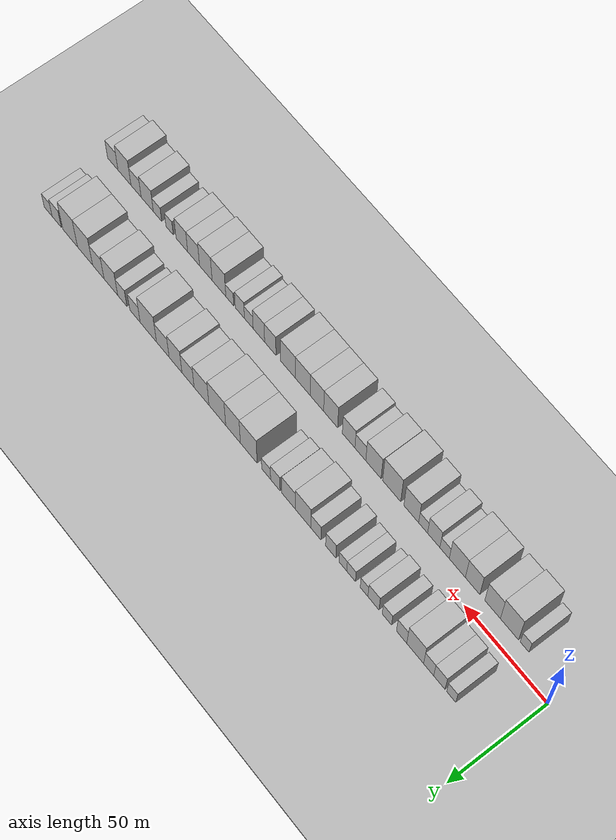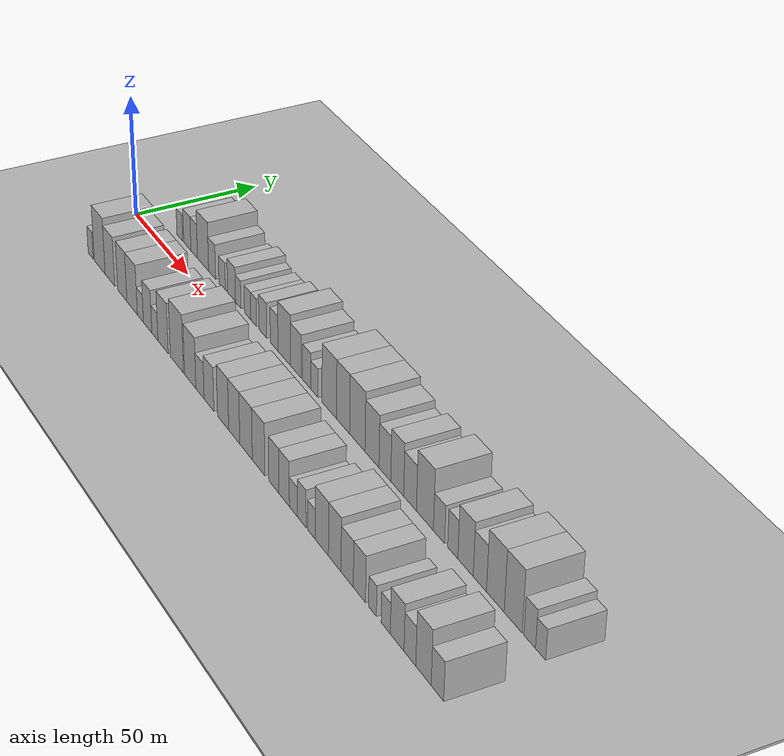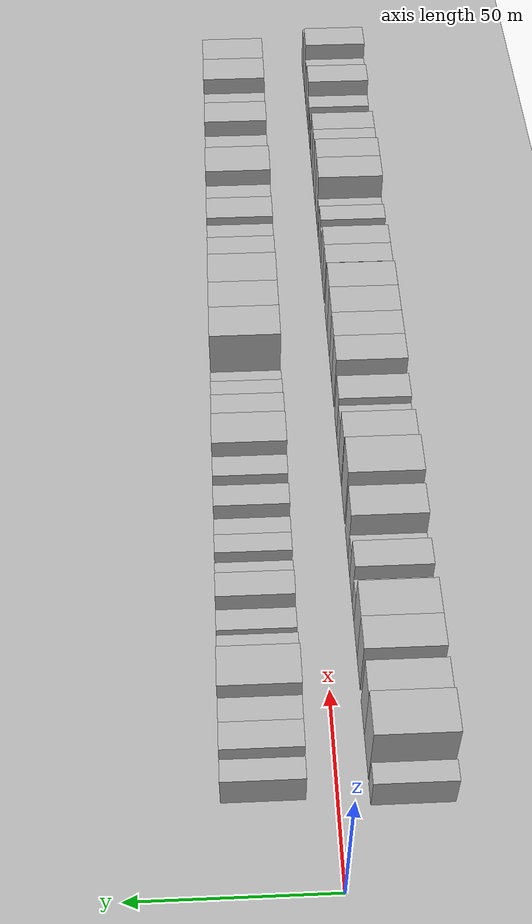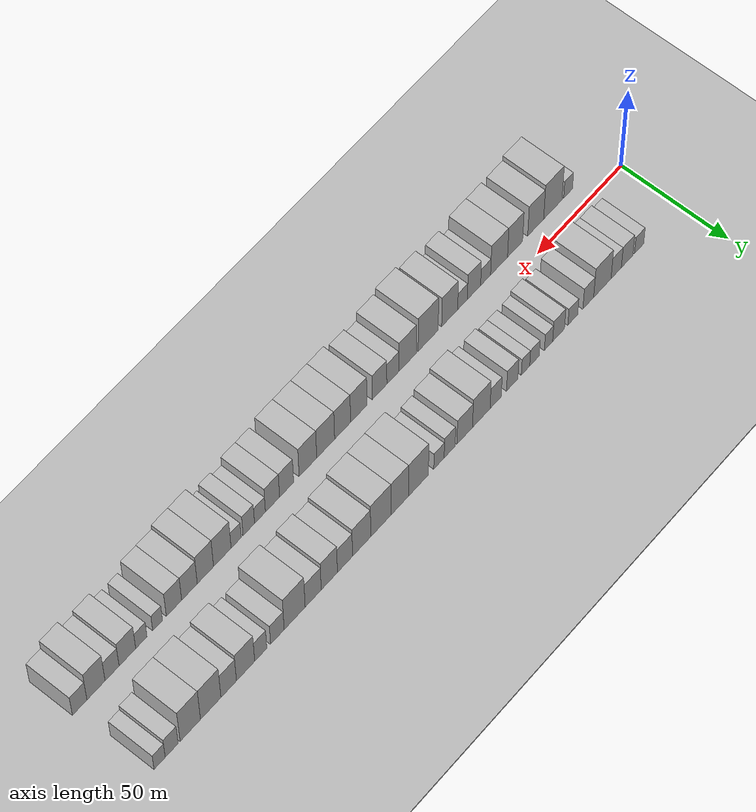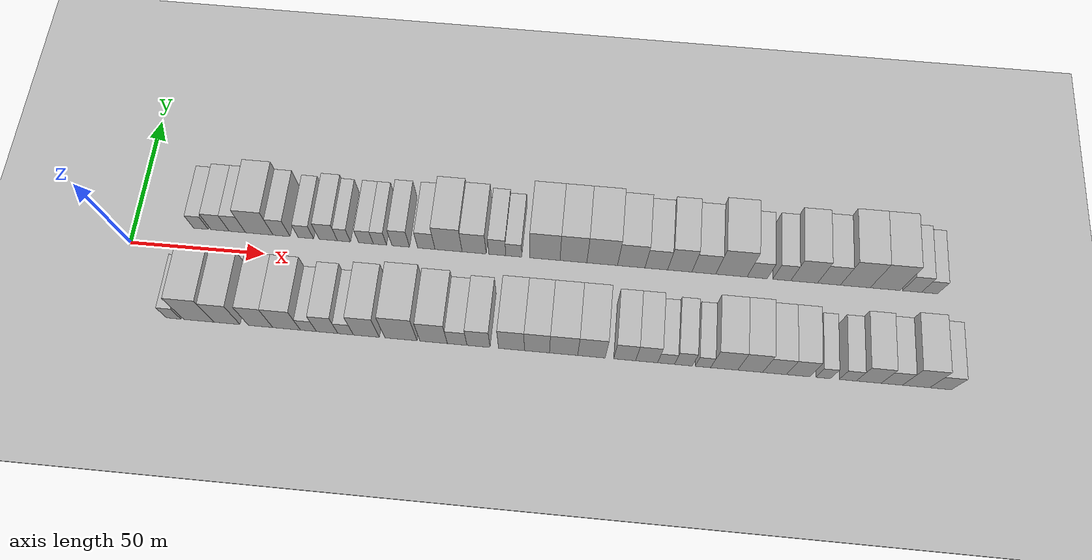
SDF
<?xml version="1.0" encoding="utf-8"?>

<sdf version="1.6">

   <world name="default">

      <gui fullscreen="0">

         <camera name="user_camera">

            <pose>-15 0 4.57585 0 0 0</pose>

            <view_controller>orbit</view_controller>

         </camera>

      </gui>

      <scene>

         <sky>

           <clouds>

             <speed>12</speed>

           </clouds>

         </sky>

         <ambient>0.4 0.4 0.4 1</ambient>

         <background>0.7 0.7 0.7 1</background>

         <shadows>1</shadows>

      </scene>

      <gravity>0 0 -9.8066</gravity>

      <magnetic_field>6e-06 2.3e-05 -4.2e-05</magnetic_field>

      <physics default="0" name="default_physics" type="ode">

         <ode>

            <solver>

               <type>quick</type>

               <iters>10</iters>

               <sor>1.0</sor>

               <use_dynamic_moi_rescaling>0</use_dynamic_moi_rescaling>

            </solver>

            <constraints>

               <cfm>0</cfm>

               <erp>0.2</erp>

               <contact_max_correcting_vel>100</contact_max_correcting_vel>

               <contact_surface_layer>0.001</contact_surface_layer>

            </constraints>

         </ode>

         <max_step_size>0.004</max_step_size>

         <real_time_factor>1</real_time_factor>

         <real_time_update_rate>250</real_time_update_rate>

      </physics>

      <light name="sun" type="directional">

         <cast_shadows>1</cast_shadows>

         <pose>0 0 10 0 0 0</pose>

         <diffuse>0.8 0.8 0.8 1</diffuse>

         <specular>0.2 0.2 0.2 1</specular>

         <attenuation>

            <range>1000</range>

            <constant>0.9</constant>

            <linear>0.01</linear>

            <quadratic>0.001</quadratic>

         </attenuation>

         <direction>-0.5 0.1 -0.9</direction>

      </light>

      <include>

         <name>ground_plane_1</name>

         <uri>model://HANNAS_ground_plane</uri>

         <pose>0 0 0  0 0 0</pose>

      </include>

      <include>

         <name>ground_plane_2</name>

         <uri>model://HANNAS_ground_plane</uri>

         <pose>100 0 0  0 0 0</pose>

      </include>

      <model name="building_1">

         <static>1</static>

         <pose frame="">24.7441 17.5000 0 0.000000 0.000000 1.570796</pose>

         <link name="link">

            <pose frame="">0 0 6.00 0 0 0</pose>

            <collision name="collision">

               <geometry>

                  <box>

                     <size>20.0000 5.4882 12.0000</size>

                  </box>

               </geometry>

               <max_contacts>10</max_contacts>

               <surface>

                  <contact>

                     <ode/>

                  </contact>

                  <bounce/>

                  <friction>

                     <torsional>

                        <ode/>

                     </torsional>

                     <ode/>

                  </friction>

               </surface>

            </collision>

            <visual name="visual">

               <cast_shadows>0</cast_shadows>

               <geometry>

                  <box>

                     <size>20.0000 5.4882 12.0000</size>

                  </box>

               </geometry>

               <material>

                  <script>

                     <uri>model://HANNAS_wall/materials/scripts</uri>

                     <uri>model://HANNAS_wall/materials/textures</uri>

                     <name>vrc/HANNAS_wall</name>

                  </script>

               </material>

            </visual>

            <self_collide>0</self_collide>

            <enable_wind>0</enable_wind>

            <kinematic>0</kinematic>

         </link>

      </model>

      <model name="building_2">

         <static>1</static>

         <pose frame="">31.9171 17.5000 0 0.000000 0.000000 1.570796</pose>

         <link name="link">

            <pose frame="">0 0 7.50 0 0 0</pose>

            <collision name="collision">

               <geometry>

                  <box>

                     <size>20.0000 6.8579 15.0000</size>

                  </box>

               </geometry>

               <max_contacts>10</max_contacts>

               <surface>

                  <contact>

                     <ode/>

                  </contact>

                  <bounce/>

                  <friction>

                     <torsional>

                        <ode/>

                     </torsional>

                     <ode/>

                  </friction>

               </surface>

            </collision>

            <visual name="visual">

               <cast_shadows>0</cast_shadows>

               <geometry>

                  <box>

                     <size>20.0000 6.8579 15.0000</size>

                  </box>

               </geometry>

               <material>

                  <script>

                     <uri>model://HANNAS_wall/materials/scripts</uri>

                     <uri>model://HANNAS_wall/materials/textures</uri>

                     <name>vrc/HANNAS_wall</name>

                  </script>

               </material>

            </visual>

            <self_collide>0</self_collide>

            <enable_wind>0</enable_wind>

            <kinematic>0</kinematic>

         </link>

      </model>

      <model name="building_3">

         <static>1</static>

         <pose frame="">38.4035 17.5000 0 0.000000 0.000000 1.570796</pose>

         <link name="link">

            <pose frame="">0 0 7.50 0 0 0</pose>

            <collision name="collision">

               <geometry>

                  <box>

                     <size>20.0000 6.1148 15.0000</size>

                  </box>

               </geometry>

               <max_contacts>10</max_contacts>

               <surface>

                  <contact>

                     <ode/>

                  </contact>

                  <bounce/>

                  <friction>

                     <torsional>

                        <ode/>

                     </torsional>

                     <ode/>

                  </friction>

               </surface>

            </collision>

            <visual name="visual">

               <cast_shadows>0</cast_shadows>

               <geometry>

                  <box>

                     <size>20.0000 6.1148 15.0000</size>

                  </box>

               </geometry>

               <material>

                  <script>

                     <uri>model://HANNAS_wall/materials/scripts</uri>

                     <uri>model://HANNAS_wall/materials/textures</uri>

                     <name>vrc/HANNAS_wall</name>

                  </script>

               </material>

            </visual>

            <self_collide>0</self_collide>

            <enable_wind>0</enable_wind>

            <kinematic>0</kinematic>

         </link>

      </model>

      <model name="building_4">

         <static>1</static>

         <pose frame="">46.6071 17.5000 0 0.000000 0.000000 1.570796</pose>

         <link name="link">

            <pose frame="">0 0 10.50 0 0 0</pose>

            <collision name="collision">

               <geometry>

                  <box>

                     <size>20.0000 10.2924 21.0000</size>

                  </box>

               </geometry>

               <max_contacts>10</max_contacts>

               <surface>

                  <contact>

                     <ode/>

                  </contact>

                  <bounce/>

                  <friction>

                     <torsional>

                        <ode/>

                     </torsional>

                     <ode/>

                  </friction>

               </surface>

            </collision>

            <visual name="visual">

               <cast_shadows>0</cast_shadows>

               <geometry>

                  <box>

                     <size>20.0000 10.2924 21.0000</size>

                  </box>

               </geometry>

               <material>

                  <script>

                     <uri>model://HANNAS_wall/materials/scripts</uri>

                     <uri>model://HANNAS_wall/materials/textures</uri>

                     <name>vrc/HANNAS_wall</name>

                  </script>

               </material>

            </visual>

            <self_collide>0</self_collide>

            <enable_wind>0</enable_wind>

            <kinematic>0</kinematic>

         </link>

      </model>

      <model name="building_5">

         <static>1</static>

         <pose frame="">54.9240 17.5000 0 0.000000 0.000000 1.570796</pose>

         <link name="link">

            <pose frame="">0 0 7.50 0 0 0</pose>

            <collision name="collision">

               <geometry>

                  <box>

                     <size>20.0000 6.3415 15.0000</size>

                  </box>

               </geometry>

               <max_contacts>10</max_contacts>

               <surface>

                  <contact>

                     <ode/>

                  </contact>

                  <bounce/>

                  <friction>

                     <torsional>

                        <ode/>

                     </torsional>

                     <ode/>

                  </friction>

               </surface>

            </collision>

            <visual name="visual">

               <cast_shadows>0</cast_shadows>

               <geometry>

                  <box>

                     <size>20.0000 6.3415 15.0000</size>

                  </box>

               </geometry>

               <material>

                  <script>

                     <uri>model://HANNAS_wall/materials/scripts</uri>

                     <uri>model://HANNAS_wall/materials/textures</uri>

                     <name>vrc/HANNAS_wall</name>

                  </script>

               </material>

            </visual>

            <self_collide>0</self_collide>

            <enable_wind>0</enable_wind>

            <kinematic>0</kinematic>

         </link>

      </model>

      <model name="building_6">

         <static>1</static>

         <pose frame="">63.9920 17.5000 0 0.000000 0.000000 1.570796</pose>

         <link name="link">

            <pose frame="">0 0 6.00 0 0 0</pose>

            <collision name="collision">

               <geometry>

                  <box>

                     <size>20.0000 5.7946 12.0000</size>

                  </box>

               </geometry>

               <max_contacts>10</max_contacts>

               <surface>

                  <contact>

                     <ode/>

                  </contact>

                  <bounce/>

                  <friction>

                     <torsional>

                        <ode/>

                     </torsional>

                     <ode/>

                  </friction>

               </surface>

            </collision>

            <visual name="visual">

               <cast_shadows>0</cast_shadows>

               <geometry>

                  <box>

                     <size>20.0000 5.7946 12.0000</size>

                  </box>

               </geometry>

               <material>

                  <script>

                     <uri>model://HANNAS_wall/materials/scripts</uri>

                     <uri>model://HANNAS_wall/materials/textures</uri>

                     <name>vrc/HANNAS_wall</name>

                  </script>

               </material>

            </visual>

            <self_collide>0</self_collide>

            <enable_wind>0</enable_wind>

            <kinematic>0</kinematic>

         </link>

      </model>

      <model name="building_7">

         <static>1</static>

         <pose frame="">72.3332 17.5000 0 0.000000 0.000000 1.570796</pose>

         <link name="link">

            <pose frame="">0 0 7.50 0 0 0</pose>

            <collision name="collision">

               <geometry>

                  <box>

                     <size>20.0000 6.8878 15.0000</size>

                  </box>

               </geometry>

               <max_contacts>10</max_contacts>

               <surface>

                  <contact>

                     <ode/>

                  </contact>

                  <bounce/>

                  <friction>

                     <torsional>

                        <ode/>

                     </torsional>

                     <ode/>

                  </friction>

               </surface>

            </collision>

            <visual name="visual">

               <cast_shadows>0</cast_shadows>

               <geometry>

                  <box>

                     <size>20.0000 6.8878 15.0000</size>

                  </box>

               </geometry>

               <material>

                  <script>

                     <uri>model://HANNAS_wall/materials/scripts</uri>

                     <uri>model://HANNAS_wall/materials/textures</uri>

                     <name>vrc/HANNAS_wall</name>

                  </script>

               </material>

            </visual>

            <self_collide>0</self_collide>

            <enable_wind>0</enable_wind>

            <kinematic>0</kinematic>

         </link>

      </model>

      <model name="building_8">

         <static>1</static>

         <pose frame="">78.1854 17.5000 0 0.000000 0.000000 1.570796</pose>

         <link name="link">

            <pose frame="">0 0 6.00 0 0 0</pose>

            <collision name="collision">

               <geometry>

                  <box>

                     <size>20.0000 4.8165 12.0000</size>

                  </box>

               </geometry>

               <max_contacts>10</max_contacts>

               <surface>

                  <contact>

                     <ode/>

                  </contact>

                  <bounce/>

                  <friction>

                     <torsional>

                        <ode/>

                     </torsional>

                     <ode/>

                  </friction>

               </surface>

            </collision>

            <visual name="visual">

               <cast_shadows>0</cast_shadows>

               <geometry>

                  <box>

                     <size>20.0000 4.8165 12.0000</size>

                  </box>

               </geometry>

               <material>

                  <script>

                     <uri>model://HANNAS_wall/materials/scripts</uri>

                     <uri>model://HANNAS_wall/materials/textures</uri>

                     <name>vrc/HANNAS_wall</name>

                  </script>

               </material>

            </visual>

            <self_collide>0</self_collide>

            <enable_wind>0</enable_wind>

            <kinematic>0</kinematic>

         </link>

      </model>

      <model name="building_9">

         <static>1</static>

         <pose frame="">86.3414 17.5000 0 0.000000 0.000000 1.570796</pose>

         <link name="link">

            <pose frame="">0 0 6.00 0 0 0</pose>

            <collision name="collision">

               <geometry>

                  <box>

                     <size>20.0000 5.4956 12.0000</size>

                  </box>

               </geometry>

               <max_contacts>10</max_contacts>

               <surface>

                  <contact>

                     <ode/>

                  </contact>

                  <bounce/>

                  <friction>

                     <torsional>

                        <ode/>

                     </torsional>

                     <ode/>

                  </friction>

               </surface>

            </collision>

            <visual name="visual">

               <cast_shadows>0</cast_shadows>

               <geometry>

                  <box>

                     <size>20.0000 5.4956 12.0000</size>

                  </box>

               </geometry>

               <material>

                  <script>

                     <uri>model://HANNAS_wall/materials/scripts</uri>

                     <uri>model://HANNAS_wall/materials/textures</uri>

                     <name>vrc/HANNAS_wall</name>

                  </script>

               </material>

            </visual>

            <self_collide>0</self_collide>

            <enable_wind>0</enable_wind>

            <kinematic>0</kinematic>

         </link>

      </model>

      <model name="building_10">

         <static>1</static>

         <pose frame="">91.5210 17.5000 0 0.000000 0.000000 1.570796</pose>

         <link name="link">

            <pose frame="">0 0 6.00 0 0 0</pose>

            <collision name="collision">

               <geometry>

                  <box>

                     <size>20.0000 4.8635 12.0000</size>

                  </box>

               </geometry>

               <max_contacts>10</max_contacts>

               <surface>

                  <contact>

                     <ode/>

                  </contact>

                  <bounce/>

                  <friction>

                     <torsional>

                        <ode/>

                     </torsional>

                     <ode/>

                  </friction>

               </surface>

            </collision>

            <visual name="visual">

               <cast_shadows>0</cast_shadows>

               <geometry>

                  <box>

                     <size>20.0000 4.8635 12.0000</size>

                  </box>

               </geometry>

               <material>

                  <script>

                     <uri>model://HANNAS_wall/materials/scripts</uri>

                     <uri>model://HANNAS_wall/materials/textures</uri>

                     <name>vrc/HANNAS_wall</name>

                  </script>

               </material>

            </visual>

            <self_collide>0</self_collide>

            <enable_wind>0</enable_wind>

            <kinematic>0</kinematic>

         </link>

      </model>

      <model name="building_11">

         <static>1</static>

         <pose frame="">99.2173 17.5000 0 0.000000 0.000000 1.570796</pose>

         <link name="link">

            <pose frame="">0 0 7.50 0 0 0</pose>

            <collision name="collision">

               <geometry>

                  <box>

                     <size>20.0000 6.5292 15.0000</size>

                  </box>

               </geometry>

               <max_contacts>10</max_contacts>

               <surface>

                  <contact>

                     <ode/>

                  </contact>

                  <bounce/>

                  <friction>

                     <torsional>

                        <ode/>

                     </torsional>

                     <ode/>

                  </friction>

               </surface>

            </collision>

            <visual name="visual">

               <cast_shadows>0</cast_shadows>

               <geometry>

                  <box>

                     <size>20.0000 6.5292 15.0000</size>

                  </box>

               </geometry>

               <material>

                  <script>

                     <uri>model://HANNAS_wall/materials/scripts</uri>

                     <uri>model://HANNAS_wall/materials/textures</uri>

                     <name>vrc/HANNAS_wall</name>

                  </script>

               </material>

            </visual>

            <self_collide>0</self_collide>

            <enable_wind>0</enable_wind>

            <kinematic>0</kinematic>

         </link>

      </model>

      <model name="building_12">

         <static>1</static>

         <pose frame="">108.6704 17.5000 0 0.000000 0.000000 1.570796</pose>

         <link name="link">

            <pose frame="">0 0 7.50 0 0 0</pose>

            <collision name="collision">

               <geometry>

                  <box>

                     <size>20.0000 6.3769 15.0000</size>

                  </box>

               </geometry>

               <max_contacts>10</max_contacts>

               <surface>

                  <contact>

                     <ode/>

                  </contact>

                  <bounce/>

                  <friction>

                     <torsional>

                        <ode/>

                     </torsional>

                     <ode/>

                  </friction>

               </surface>

            </collision>

            <visual name="visual">

               <cast_shadows>0</cast_shadows>

               <geometry>

                  <box>

                     <size>20.0000 6.3769 15.0000</size>

                  </box>

               </geometry>

               <material>

                  <script>

                     <uri>model://HANNAS_wall/materials/scripts</uri>

                     <uri>model://HANNAS_wall/materials/textures</uri>

                     <name>vrc/HANNAS_wall</name>

                  </script>

               </material>

            </visual>

            <self_collide>0</self_collide>

            <enable_wind>0</enable_wind>

            <kinematic>0</kinematic>

         </link>

      </model>

      <model name="building_13">

         <static>1</static>

         <pose frame="">116.8591 17.5000 0 0.000000 0.000000 1.570796</pose>

         <link name="link">

            <pose frame="">0 0 10.50 0 0 0</pose>

            <collision name="collision">

               <geometry>

                  <box>

                     <size>20.0000 10.0005 21.0000</size>

                  </box>

               </geometry>

               <max_contacts>10</max_contacts>

               <surface>

                  <contact>

                     <ode/>

                  </contact>

                  <bounce/>

                  <friction>

                     <torsional>

                        <ode/>

                     </torsional>

                     <ode/>

                  </friction>

               </surface>

            </collision>

            <visual name="visual">

               <cast_shadows>0</cast_shadows>

               <geometry>

                  <box>

                     <size>20.0000 10.0005 21.0000</size>

                  </box>

               </geometry>

               <material>

                  <script>

                     <uri>model://HANNAS_wall/materials/scripts</uri>

                     <uri>model://HANNAS_wall/materials/textures</uri>

                     <name>vrc/HANNAS_wall</name>

                  </script>

               </material>

            </visual>

            <self_collide>0</self_collide>

            <enable_wind>0</enable_wind>

            <kinematic>0</kinematic>

         </link>

      </model>

      <model name="building_14">

         <static>1</static>

         <pose frame="">126.2873 17.5000 0 0.000000 0.000000 1.570796</pose>

         <link name="link">

            <pose frame="">0 0 9.00 0 0 0</pose>

            <collision name="collision">

               <geometry>

                  <box>

                     <size>20.0000 8.8560 18.0000</size>

                  </box>

               </geometry>

               <max_contacts>10</max_contacts>

               <surface>

                  <contact>

                     <ode/>

                  </contact>

                  <bounce/>

                  <friction>

                     <torsional>

                        <ode/>

                     </torsional>

                     <ode/>

                  </friction>

               </surface>

            </collision>

            <visual name="visual">

               <cast_shadows>0</cast_shadows>

               <geometry>

                  <box>

                     <size>20.0000 8.8560 18.0000</size>

                  </box>

               </geometry>

               <material>

                  <script>

                     <uri>model://HANNAS_wall/materials/scripts</uri>

                     <uri>model://HANNAS_wall/materials/textures</uri>

                     <name>vrc/HANNAS_wall</name>

                  </script>

               </material>

            </visual>

            <self_collide>0</self_collide>

            <enable_wind>0</enable_wind>

            <kinematic>0</kinematic>

         </link>

      </model>

      <model name="building_15">

         <static>1</static>

         <pose frame="">134.8201 17.5000 0 0.000000 0.000000 1.570796</pose>

         <link name="link">

            <pose frame="">0 0 7.50 0 0 0</pose>

            <collision name="collision">

               <geometry>

                  <box>

                     <size>20.0000 6.2095 15.0000</size>

                  </box>

               </geometry>

               <max_contacts>10</max_contacts>

               <surface>

                  <contact>

                     <ode/>

                  </contact>

                  <bounce/>

                  <friction>

                     <torsional>

                        <ode/>

                     </torsional>

                     <ode/>

                  </friction>

               </surface>

            </collision>

            <visual name="visual">

               <cast_shadows>0</cast_shadows>

               <geometry>

                  <box>

                     <size>20.0000 6.2095 15.0000</size>

                  </box>

               </geometry>

               <material>

                  <script>

                     <uri>model://HANNAS_wall/materials/scripts</uri>

                     <uri>model://HANNAS_wall/materials/textures</uri>

                     <name>vrc/HANNAS_wall</name>

                  </script>

               </material>

            </visual>

            <self_collide>0</self_collide>

            <enable_wind>0</enable_wind>

            <kinematic>0</kinematic>

         </link>

      </model>

      <model name="building_16">

         <static>1</static>

         <pose frame="">140.8430 17.5000 0 0.000000 0.000000 1.570796</pose>

         <link name="link">

            <pose frame="">0 0 6.00 0 0 0</pose>

            <collision name="collision">

               <geometry>

                  <box>

                     <size>20.0000 5.8364 12.0000</size>

                  </box>

               </geometry>

               <max_contacts>10</max_contacts>

               <surface>

                  <contact>

                     <ode/>

                  </contact>

                  <bounce/>

                  <friction>

                     <torsional>

                        <ode/>

                     </torsional>

                     <ode/>

                  </friction>

               </surface>

            </collision>

            <visual name="visual">

               <cast_shadows>0</cast_shadows>

               <geometry>

                  <box>

                     <size>20.0000 5.8364 12.0000</size>

                  </box>

               </geometry>

               <material>

                  <script>

                     <uri>model://HANNAS_wall/materials/scripts</uri>

                     <uri>model://HANNAS_wall/materials/textures</uri>

                     <name>vrc/HANNAS_wall</name>

                  </script>

               </material>

            </visual>

            <self_collide>0</self_collide>

            <enable_wind>0</enable_wind>

            <kinematic>0</kinematic>

         </link>

      </model>

      <model name="building_17">

         <static>1</static>

         <pose frame="">152.2762 17.5000 0 0.000000 0.000000 1.570796</pose>

         <link name="link">

            <pose frame="">0 0 12.00 0 0 0</pose>

            <collision name="collision">

               <geometry>

                  <box>

                     <size>20.0000 11.0300 24.0000</size>

                  </box>

               </geometry>

               <max_contacts>10</max_contacts>

               <surface>

                  <contact>

                     <ode/>

                  </contact>

                  <bounce/>

                  <friction>

                     <torsional>

                        <ode/>

                     </torsional>

                     <ode/>

                  </friction>

               </surface>

            </collision>

            <visual name="visual">

               <cast_shadows>0</cast_shadows>

               <geometry>

                  <box>

                     <size>20.0000 11.0300 24.0000</size>

                  </box>

               </geometry>

               <material>

                  <script>

                     <uri>model://HANNAS_wall/materials/scripts</uri>

                     <uri>model://HANNAS_wall/materials/textures</uri>

                     <name>vrc/HANNAS_wall</name>

                  </script>

               </material>

            </visual>

            <self_collide>0</self_collide>

            <enable_wind>0</enable_wind>

            <kinematic>0</kinematic>

         </link>

      </model>

      <model name="building_18">

         <static>1</static>

         <pose frame="">162.6787 17.5000 0 0.000000 0.000000 1.570796</pose>

         <link name="link">

            <pose frame="">0 0 12.00 0 0 0</pose>

            <collision name="collision">

               <geometry>

                  <box>

                     <size>20.0000 9.7751 24.0000</size>

                  </box>

               </geometry>

               <max_contacts>10</max_contacts>

               <surface>

                  <contact>

                     <ode/>

                  </contact>

                  <bounce/>

                  <friction>

                     <torsional>

                        <ode/>

                     </torsional>

                     <ode/>

                  </friction>

               </surface>

            </collision>

            <visual name="visual">

               <cast_shadows>0</cast_shadows>

               <geometry>

                  <box>

                     <size>20.0000 9.7751 24.0000</size>

                  </box>

               </geometry>

               <material>

                  <script>

                     <uri>model://HANNAS_wall/materials/scripts</uri>

                     <uri>model://HANNAS_wall/materials/textures</uri>

                     <name>vrc/HANNAS_wall</name>

                  </script>

               </material>

            </visual>

            <self_collide>0</self_collide>

            <enable_wind>0</enable_wind>

            <kinematic>0</kinematic>

         </link>

      </model>

      <model name="building_19">

         <static>1</static>

         <pose frame="">173.1793 17.5000 0 0.000000 0.000000 1.570796</pose>

         <link name="link">

            <pose frame="">0 0 12.00 0 0 0</pose>

            <collision name="collision">

               <geometry>

                  <box>

                     <size>20.0000 11.2261 24.0000</size>

                  </box>

               </geometry>

               <max_contacts>10</max_contacts>

               <surface>

                  <contact>

                     <ode/>

                  </contact>

                  <bounce/>

                  <friction>

                     <torsional>

                        <ode/>

                     </torsional>

                     <ode/>

                  </friction>

               </surface>

            </collision>

            <visual name="visual">

               <cast_shadows>0</cast_shadows>

               <geometry>

                  <box>

                     <size>20.0000 11.2261 24.0000</size>

                  </box>

               </geometry>

               <material>

                  <script>

                     <uri>model://HANNAS_wall/materials/scripts</uri>

                     <uri>model://HANNAS_wall/materials/textures</uri>

                     <name>vrc/HANNAS_wall</name>

                  </script>

               </material>

            </visual>

            <self_collide>0</self_collide>

            <enable_wind>0</enable_wind>

            <kinematic>0</kinematic>

         </link>

      </model>

      <model name="building_20">

         <static>1</static>

         <pose frame="">183.7918 17.5000 0 0.000000 0.000000 1.570796</pose>

         <link name="link">

            <pose frame="">0 0 10.50 0 0 0</pose>

            <collision name="collision">

               <geometry>

                  <box>

                     <size>20.0000 9.9990 21.0000</size>

                  </box>

               </geometry>

               <max_contacts>10</max_contacts>

               <surface>

                  <contact>

                     <ode/>

                  </contact>

                  <bounce/>

                  <friction>

                     <torsional>

                        <ode/>

                     </torsional>

                     <ode/>

                  </friction>

               </surface>

            </collision>

            <visual name="visual">

               <cast_shadows>0</cast_shadows>

               <geometry>

                  <box>

                     <size>20.0000 9.9990 21.0000</size>

                  </box>

               </geometry>

               <material>

                  <script>

                     <uri>model://HANNAS_wall/materials/scripts</uri>

                     <uri>model://HANNAS_wall/materials/textures</uri>

                     <name>vrc/HANNAS_wall</name>

                  </script>

               </material>

            </visual>

            <self_collide>0</self_collide>

            <enable_wind>0</enable_wind>

            <kinematic>0</kinematic>

         </link>

      </model>

      <model name="building_21">

         <static>1</static>

         <pose frame="">192.9205 17.5000 0 0.000000 0.000000 1.570796</pose>

         <link name="link">

            <pose frame="">0 0 9.00 0 0 0</pose>

            <collision name="collision">

               <geometry>

                  <box>

                     <size>20.0000 8.2584 18.0000</size>

                  </box>

               </geometry>

               <max_contacts>10</max_contacts>

               <surface>

                  <contact>

                     <ode/>

                  </contact>

                  <bounce/>

                  <friction>

                     <torsional>

                        <ode/>

                     </torsional>

                     <ode/>

                  </friction>

               </surface>

            </collision>

            <visual name="visual">

               <cast_shadows>0</cast_shadows>

               <geometry>

                  <box>

                     <size>20.0000 8.2584 18.0000</size>

                  </box>

               </geometry>

               <material>

                  <script>

                     <uri>model://HANNAS_wall/materials/scripts</uri>

                     <uri>model://HANNAS_wall/materials/textures</uri>

                     <name>vrc/HANNAS_wall</name>

                  </script>

               </material>

            </visual>

            <self_collide>0</self_collide>

            <enable_wind>0</enable_wind>

            <kinematic>0</kinematic>

         </link>

      </model>

      <model name="building_22">

         <static>1</static>

         <pose frame="">201.4533 17.5000 0 0.000000 0.000000 1.570796</pose>

         <link name="link">

            <pose frame="">0 0 10.50 0 0 0</pose>

            <collision name="collision">

               <geometry>

                  <box>

                     <size>20.0000 8.8072 21.0000</size>

                  </box>

               </geometry>

               <max_contacts>10</max_contacts>

               <surface>

                  <contact>

                     <ode/>

                  </contact>

                  <bounce/>

                  <friction>

                     <torsional>

                        <ode/>

                     </torsional>

                     <ode/>

                  </friction>

               </surface>

            </collision>

            <visual name="visual">

               <cast_shadows>0</cast_shadows>

               <geometry>

                  <box>

                     <size>20.0000 8.8072 21.0000</size>

                  </box>

               </geometry>

               <material>

                  <script>

                     <uri>model://HANNAS_wall/materials/scripts</uri>

                     <uri>model://HANNAS_wall/materials/textures</uri>

                     <name>vrc/HANNAS_wall</name>

                  </script>

               </material>

            </visual>

            <self_collide>0</self_collide>

            <enable_wind>0</enable_wind>

            <kinematic>0</kinematic>

         </link>

      </model>

      <model name="building_23">

         <static>1</static>

         <pose frame="">210.2037 17.5000 0 0.000000 0.000000 1.570796</pose>

         <link name="link">

            <pose frame="">0 0 9.00 0 0 0</pose>

            <collision name="collision">

               <geometry>

                  <box>

                     <size>20.0000 8.6935 18.0000</size>

                  </box>

               </geometry>

               <max_contacts>10</max_contacts>

               <surface>

                  <contact>

                     <ode/>

                  </contact>

                  <bounce/>

                  <friction>

                     <torsional>

                        <ode/>

                     </torsional>

                     <ode/>

                  </friction>

               </surface>

            </collision>

            <visual name="visual">

               <cast_shadows>0</cast_shadows>

               <geometry>

                  <box>

                     <size>20.0000 8.6935 18.0000</size>

                  </box>

               </geometry>

               <material>

                  <script>

                     <uri>model://HANNAS_wall/materials/scripts</uri>

                     <uri>model://HANNAS_wall/materials/textures</uri>

                     <name>vrc/HANNAS_wall</name>

                  </script>

               </material>

            </visual>

            <self_collide>0</self_collide>

            <enable_wind>0</enable_wind>

            <kinematic>0</kinematic>

         </link>

      </model>

      <model name="building_24">

         <static>1</static>

         <pose frame="">220.1891 17.5000 0 0.000000 0.000000 1.570796</pose>

         <link name="link">

            <pose frame="">0 0 12.00 0 0 0</pose>

            <collision name="collision">

               <geometry>

                  <box>

                     <size>20.0000 11.2774 24.0000</size>

                  </box>

               </geometry>

               <max_contacts>10</max_contacts>

               <surface>

                  <contact>

                     <ode/>

                  </contact>

                  <bounce/>

                  <friction>

                     <torsional>

                        <ode/>

                     </torsional>

                     <ode/>

                  </friction>

               </surface>

            </collision>

            <visual name="visual">

               <cast_shadows>0</cast_shadows>

               <geometry>

                  <box>

                     <size>20.0000 11.2774 24.0000</size>

                  </box>

               </geometry>

               <material>

                  <script>

                     <uri>model://HANNAS_wall/materials/scripts</uri>

                     <uri>model://HANNAS_wall/materials/textures</uri>

                     <name>vrc/HANNAS_wall</name>

                  </script>

               </material>

            </visual>

            <self_collide>0</self_collide>

            <enable_wind>0</enable_wind>

            <kinematic>0</kinematic>

         </link>

      </model>

      <model name="building_25">

         <static>1</static>

         <pose frame="">229.4601 17.5000 0 0.000000 0.000000 1.570796</pose>

         <link name="link">

            <pose frame="">0 0 7.50 0 0 0</pose>

            <collision name="collision">

               <geometry>

                  <box>

                     <size>20.0000 7.2645 15.0000</size>

                  </box>

               </geometry>

               <max_contacts>10</max_contacts>

               <surface>

                  <contact>

                     <ode/>

                  </contact>

                  <bounce/>

                  <friction>

                     <torsional>

                        <ode/>

                     </torsional>

                     <ode/>

                  </friction>

               </surface>

            </collision>

            <visual name="visual">

               <cast_shadows>0</cast_shadows>

               <geometry>

                  <box>

                     <size>20.0000 7.2645 15.0000</size>

                  </box>

               </geometry>

               <material>

                  <script>

                     <uri>model://HANNAS_wall/materials/scripts</uri>

                     <uri>model://HANNAS_wall/materials/textures</uri>

                     <name>vrc/HANNAS_wall</name>

                  </script>

               </material>

            </visual>

            <self_collide>0</self_collide>

            <enable_wind>0</enable_wind>

            <kinematic>0</kinematic>

         </link>

      </model>

      <model name="building_26">

         <static>1</static>

         <pose frame="">238.3251 17.5000 0 0.000000 0.000000 1.570796</pose>

         <link name="link">

            <pose frame="">0 0 7.50 0 0 0</pose>

            <collision name="collision">

               <geometry>

                  <box>

                     <size>20.0000 6.4654 15.0000</size>

                  </box>

               </geometry>

               <max_contacts>10</max_contacts>

               <surface>

                  <contact>

                     <ode/>

                  </contact>

                  <bounce/>

                  <friction>

                     <torsional>

                        <ode/>

                     </torsional>

                     <ode/>

                  </friction>

               </surface>

            </collision>

            <visual name="visual">

               <cast_shadows>0</cast_shadows>

               <geometry>

                  <box>

                     <size>20.0000 6.4654 15.0000</size>

                  </box>

               </geometry>

               <material>

                  <script>

                     <uri>model://HANNAS_wall/materials/scripts</uri>

                     <uri>model://HANNAS_wall/materials/textures</uri>

                     <name>vrc/HANNAS_wall</name>

                  </script>

               </material>

            </visual>

            <self_collide>0</self_collide>

            <enable_wind>0</enable_wind>

            <kinematic>0</kinematic>

         </link>

      </model>

      <model name="building_27">

         <static>1</static>

         <pose frame="">246.3901 17.5000 0 0.000000 0.000000 1.570796</pose>

         <link name="link">

            <pose frame="">0 0 10.50 0 0 0</pose>

            <collision name="collision">

               <geometry>

                  <box>

                     <size>20.0000 9.6647 21.0000</size>

                  </box>

               </geometry>

               <max_contacts>10</max_contacts>

               <surface>

                  <contact>

                     <ode/>

                  </contact>

                  <bounce/>

                  <friction>

                     <torsional>

                        <ode/>

                     </torsional>

                     <ode/>

                  </friction>

               </surface>

            </collision>

            <visual name="visual">

               <cast_shadows>0</cast_shadows>

               <geometry>

                  <box>

                     <size>20.0000 9.6647 21.0000</size>

                  </box>

               </geometry>

               <material>

                  <script>

                     <uri>model://HANNAS_wall/materials/scripts</uri>

                     <uri>model://HANNAS_wall/materials/textures</uri>

                     <name>vrc/HANNAS_wall</name>

                  </script>

               </material>

            </visual>

            <self_collide>0</self_collide>

            <enable_wind>0</enable_wind>

            <kinematic>0</kinematic>

         </link>

      </model>

      <model name="building_28">

         <static>1</static>

         <pose frame="">255.3139 17.5000 0 0.000000 0.000000 1.570796</pose>

         <link name="link">

            <pose frame="">0 0 9.00 0 0 0</pose>

            <collision name="collision">

               <geometry>

                  <box>

                     <size>20.0000 8.1829 18.0000</size>

                  </box>

               </geometry>

               <max_contacts>10</max_contacts>

               <surface>

                  <contact>

                     <ode/>

                  </contact>

                  <bounce/>

                  <friction>

                     <torsional>

                        <ode/>

                     </torsional>

                     <ode/>

                  </friction>

               </surface>

            </collision>

            <visual name="visual">

               <cast_shadows>0</cast_shadows>

               <geometry>

                  <box>

                     <size>20.0000 8.1829 18.0000</size>

                  </box>

               </geometry>

               <material>

                  <script>

                     <uri>model://HANNAS_wall/materials/scripts</uri>

                     <uri>model://HANNAS_wall/materials/textures</uri>

                     <name>vrc/HANNAS_wall</name>

                  </script>

               </material>

            </visual>

            <self_collide>0</self_collide>

            <enable_wind>0</enable_wind>

            <kinematic>0</kinematic>

         </link>

      </model>

      <model name="building_29">

         <static>1</static>

         <pose frame="">264.7660 17.5000 0 0.000000 0.000000 1.570796</pose>

         <link name="link">

            <pose frame="">0 0 12.00 0 0 0</pose>

            <collision name="collision">

               <geometry>

                  <box>

                     <size>20.0000 10.7212 24.0000</size>

                  </box>

               </geometry>

               <max_contacts>10</max_contacts>

               <surface>

                  <contact>

                     <ode/>

                  </contact>

                  <bounce/>

                  <friction>

                     <torsional>

                        <ode/>

                     </torsional>

                     <ode/>

                  </friction>

               </surface>

            </collision>

            <visual name="visual">

               <cast_shadows>0</cast_shadows>

               <geometry>

                  <box>

                     <size>20.0000 10.7212 24.0000</size>

                  </box>

               </geometry>

               <material>

                  <script>

                     <uri>model://HANNAS_wall/materials/scripts</uri>

                     <uri>model://HANNAS_wall/materials/textures</uri>

                     <name>vrc/HANNAS_wall</name>

                  </script>

               </material>

            </visual>

            <self_collide>0</self_collide>

            <enable_wind>0</enable_wind>

            <kinematic>0</kinematic>

         </link>

      </model>

      <model name="building_30">

         <static>1</static>

         <pose frame="">275.4392 17.5000 0 0.000000 0.000000 1.570796</pose>

         <link name="link">

            <pose frame="">0 0 12.00 0 0 0</pose>

            <collision name="collision">

               <geometry>

                  <box>

                     <size>20.0000 10.6250 24.0000</size>

                  </box>

               </geometry>

               <max_contacts>10</max_contacts>

               <surface>

                  <contact>

                     <ode/>

                  </contact>

                  <bounce/>

                  <friction>

                     <torsional>

                        <ode/>

                     </torsional>

                     <ode/>

                  </friction>

               </surface>

            </collision>

            <visual name="visual">

               <cast_shadows>0</cast_shadows>

               <geometry>

                  <box>

                     <size>20.0000 10.6250 24.0000</size>

                  </box>

               </geometry>

               <material>

                  <script>

                     <uri>model://HANNAS_wall/materials/scripts</uri>

                     <uri>model://HANNAS_wall/materials/textures</uri>

                     <name>vrc/HANNAS_wall</name>

                  </script>

               </material>

            </visual>

            <self_collide>0</self_collide>

            <enable_wind>0</enable_wind>

            <kinematic>0</kinematic>

         </link>

      </model>

      <model name="building_31">

         <static>1</static>

         <pose frame="">285.1096 17.5000 0 0.000000 0.000000 1.570796</pose>

         <link name="link">

            <pose frame="">0 0 7.50 0 0 0</pose>

            <collision name="collision">

               <geometry>

                  <box>

                     <size>20.0000 6.7159 15.0000</size>

                  </box>

               </geometry>

               <max_contacts>10</max_contacts>

               <surface>

                  <contact>

                     <ode/>

                  </contact>

                  <bounce/>

                  <friction>

                     <torsional>

                        <ode/>

                     </torsional>

                     <ode/>

                  </friction>

               </surface>

            </collision>

            <visual name="visual">

               <cast_shadows>0</cast_shadows>

               <geometry>

                  <box>

                     <size>20.0000 6.7159 15.0000</size>

                  </box>

               </geometry>

               <material>

                  <script>

                     <uri>model://HANNAS_wall/materials/scripts</uri>

                     <uri>model://HANNAS_wall/materials/textures</uri>

                     <name>vrc/HANNAS_wall</name>

                  </script>

               </material>

            </visual>

            <self_collide>0</self_collide>

            <enable_wind>0</enable_wind>

            <kinematic>0</kinematic>

         </link>

      </model>

      <model name="building_32">

         <static>1</static>

         <pose frame="">291.3562 17.5000 0 0.000000 0.000000 1.570796</pose>

         <link name="link">

            <pose frame="">0 0 6.00 0 0 0</pose>

            <collision name="collision">

               <geometry>

                  <box>

                     <size>20.0000 5.7774 12.0000</size>

                  </box>

               </geometry>

               <max_contacts>10</max_contacts>

               <surface>

                  <contact>

                     <ode/>

                  </contact>

                  <bounce/>

                  <friction>

                     <torsional>

                        <ode/>

                     </torsional>

                     <ode/>

                  </friction>

               </surface>

            </collision>

            <visual name="visual">

               <cast_shadows>0</cast_shadows>

               <geometry>

                  <box>

                     <size>20.0000 5.7774 12.0000</size>

                  </box>

               </geometry>

               <material>

                  <script>

                     <uri>model://HANNAS_wall/materials/scripts</uri>

                     <uri>model://HANNAS_wall/materials/textures</uri>

                     <name>vrc/HANNAS_wall</name>

                  </script>

               </material>

            </visual>

            <self_collide>0</self_collide>

            <enable_wind>0</enable_wind>

            <kinematic>0</kinematic>

         </link>

      </model>

      <model name="building_33">

         <static>1</static>

         <pose frame="">22.6224 -17.5000 0 0.000000 0.000000 1.570796</pose>

         <link name="link">

            <pose frame="">0 0 6.00 0 0 0</pose>

            <collision name="collision">

               <geometry>

                  <box>

                     <size>20.0000 5.2447 12.0000</size>

                  </box>

               </geometry>

               <max_contacts>10</max_contacts>

               <surface>

                  <contact>

                     <ode/>

                  </contact>

                  <bounce/>

                  <friction>

                     <torsional>

                        <ode/>

                     </torsional>

                     <ode/>

                  </friction>

               </surface>

            </collision>

            <visual name="visual">

               <cast_shadows>0</cast_shadows>

               <geometry>

                  <box>

                     <size>20.0000 5.2447 12.0000</size>

                  </box>

               </geometry>

               <material>

                  <script>

                     <uri>model://HANNAS_wall/materials/scripts</uri>

                     <uri>model://HANNAS_wall/materials/textures</uri>

                     <name>vrc/HANNAS_wall</name>

                  </script>

               </material>

            </visual>

            <self_collide>0</self_collide>

            <enable_wind>0</enable_wind>

            <kinematic>0</kinematic>

         </link>

      </model>

      <model name="building_34">

         <static>1</static>

         <pose frame="">31.6956 -17.5000 0 0.000000 0.000000 1.570796</pose>

         <link name="link">

            <pose frame="">0 0 12.00 0 0 0</pose>

            <collision name="collision">

               <geometry>

                  <box>

                     <size>20.0000 10.9018 24.0000</size>

                  </box>

               </geometry>

               <max_contacts>10</max_contacts>

               <surface>

                  <contact>

                     <ode/>

                  </contact>

                  <bounce/>

                  <friction>

                     <torsional>

                        <ode/>

                     </torsional>

                     <ode/>

                  </friction>

               </surface>

            </collision>

            <visual name="visual">

               <cast_shadows>0</cast_shadows>

               <geometry>

                  <box>

                     <size>20.0000 10.9018 24.0000</size>

                  </box>

               </geometry>

               <material>

                  <script>

                     <uri>model://HANNAS_wall/materials/scripts</uri>

                     <uri>model://HANNAS_wall/materials/textures</uri>

                     <name>vrc/HANNAS_wall</name>

                  </script>

               </material>

            </visual>

            <self_collide>0</self_collide>

            <enable_wind>0</enable_wind>

            <kinematic>0</kinematic>

         </link>

      </model>

      <model name="building_35">

         <static>1</static>

         <pose frame="">41.8701 -17.5000 0 0.000000 0.000000 1.570796</pose>

         <link name="link">

            <pose frame="">0 0 10.50 0 0 0</pose>

            <collision name="collision">

               <geometry>

                  <box>

                     <size>20.0000 9.4472 21.0000</size>

                  </box>

               </geometry>

               <max_contacts>10</max_contacts>

               <surface>

                  <contact>

                     <ode/>

                  </contact>

                  <bounce/>

                  <friction>

                     <torsional>

                        <ode/>

                     </torsional>

                     <ode/>

                  </friction>

               </surface>

            </collision>

            <visual name="visual">

               <cast_shadows>0</cast_shadows>

               <geometry>

                  <box>

                     <size>20.0000 9.4472 21.0000</size>

                  </box>

               </geometry>

               <material>

                  <script>

                     <uri>model://HANNAS_wall/materials/scripts</uri>

                     <uri>model://HANNAS_wall/materials/textures</uri>

                     <name>vrc/HANNAS_wall</name>

                  </script>

               </material>

            </visual>

            <self_collide>0</self_collide>

            <enable_wind>0</enable_wind>

            <kinematic>0</kinematic>

         </link>

      </model>

      <model name="building_36">

         <static>1</static>

         <pose frame="">54.0088 -17.5000 0 0.000000 0.000000 1.570796</pose>

         <link name="link">

            <pose frame="">0 0 10.50 0 0 0</pose>

            <collision name="collision">

               <geometry>

                  <box>

                     <size>20.0000 8.8303 21.0000</size>

                  </box>

               </geometry>

               <max_contacts>10</max_contacts>

               <surface>

                  <contact>

                     <ode/>

                  </contact>

                  <bounce/>

                  <friction>

                     <torsional>

                        <ode/>

                     </torsional>

                     <ode/>

                  </friction>

               </surface>

            </collision>

            <visual name="visual">

               <cast_shadows>0</cast_shadows>

               <geometry>

                  <box>

                     <size>20.0000 8.8303 21.0000</size>

                  </box>

               </geometry>

               <material>

                  <script>

                     <uri>model://HANNAS_wall/materials/scripts</uri>

                     <uri>model://HANNAS_wall/materials/textures</uri>

                     <name>vrc/HANNAS_wall</name>

                  </script>

               </material>

            </visual>

            <self_collide>0</self_collide>

            <enable_wind>0</enable_wind>

            <kinematic>0</kinematic>

         </link>

      </model>

      <model name="building_37">

         <static>1</static>

         <pose frame="">63.3813 -17.5000 0 0.000000 0.000000 1.570796</pose>

         <link name="link">

            <pose frame="">0 0 10.50 0 0 0</pose>

            <collision name="collision">

               <geometry>

                  <box>

                     <size>20.0000 9.9147 21.0000</size>

                  </box>

               </geometry>

               <max_contacts>10</max_contacts>

               <surface>

                  <contact>

                     <ode/>

                  </contact>

                  <bounce/>

                  <friction>

                     <torsional>

                        <ode/>

                     </torsional>

                     <ode/>

                  </friction>

               </surface>

            </collision>

            <visual name="visual">

               <cast_shadows>0</cast_shadows>

               <geometry>

                  <box>

                     <size>20.0000 9.9147 21.0000</size>

                  </box>

               </geometry>

               <material>

                  <script>

                     <uri>model://HANNAS_wall/materials/scripts</uri>

                     <uri>model://HANNAS_wall/materials/textures</uri>

                     <name>vrc/HANNAS_wall</name>

                  </script>

               </material>

            </visual>

            <self_collide>0</self_collide>

            <enable_wind>0</enable_wind>

            <kinematic>0</kinematic>

         </link>

      </model>

      <model name="building_38">

         <static>1</static>

         <pose frame="">71.2271 -17.5000 0 0.000000 0.000000 1.570796</pose>

         <link name="link">

            <pose frame="">0 0 6.00 0 0 0</pose>

            <collision name="collision">

               <geometry>

                  <box>

                     <size>20.0000 5.7768 12.0000</size>

                  </box>

               </geometry>

               <max_contacts>10</max_contacts>

               <surface>

                  <contact>

                     <ode/>

                  </contact>

                  <bounce/>

                  <friction>

                     <torsional>

                        <ode/>

                     </torsional>

                     <ode/>

                  </friction>

               </surface>

            </collision>

            <visual name="visual">

               <cast_shadows>0</cast_shadows>

               <geometry>

                  <box>

                     <size>20.0000 5.7768 12.0000</size>

                  </box>

               </geometry>

               <material>

                  <script>

                     <uri>model://HANNAS_wall/materials/scripts</uri>

                     <uri>model://HANNAS_wall/materials/textures</uri>

                     <name>vrc/HANNAS_wall</name>

                  </script>

               </material>

            </visual>

            <self_collide>0</self_collide>

            <enable_wind>0</enable_wind>

            <kinematic>0</kinematic>

         </link>

      </model>

      <model name="building_39">

         <static>1</static>

         <pose frame="">77.9601 -17.5000 0 0.000000 0.000000 1.570796</pose>

         <link name="link">

            <pose frame="">0 0 9.00 0 0 0</pose>

            <collision name="collision">

               <geometry>

                  <box>

                     <size>20.0000 7.6892 18.0000</size>

                  </box>

               </geometry>

               <max_contacts>10</max_contacts>

               <surface>

                  <contact>

                     <ode/>

                  </contact>

                  <bounce/>

                  <friction>

                     <torsional>

                        <ode/>

                     </torsional>

                     <ode/>

                  </friction>

               </surface>

            </collision>

            <visual name="visual">

               <cast_shadows>0</cast_shadows>

               <geometry>

                  <box>

                     <size>20.0000 7.6892 18.0000</size>

                  </box>

               </geometry>

               <material>

                  <script>

                     <uri>model://HANNAS_wall/materials/scripts</uri>

                     <uri>model://HANNAS_wall/materials/textures</uri>

                     <name>vrc/HANNAS_wall</name>

                  </script>

               </material>

            </visual>

            <self_collide>0</self_collide>

            <enable_wind>0</enable_wind>

            <kinematic>0</kinematic>

         </link>

      </model>

      <model name="building_40">

         <static>1</static>

         <pose frame="">84.5954 -17.5000 0 0.000000 0.000000 1.570796</pose>

         <link name="link">

            <pose frame="">0 0 6.00 0 0 0</pose>

            <collision name="collision">

               <geometry>

                  <box>

                     <size>20.0000 5.5814 12.0000</size>

                  </box>

               </geometry>

               <max_contacts>10</max_contacts>

               <surface>

                  <contact>

                     <ode/>

                  </contact>

                  <bounce/>

                  <friction>

                     <torsional>

                        <ode/>

                     </torsional>

                     <ode/>

                  </friction>

               </surface>

            </collision>

            <visual name="visual">

               <cast_shadows>0</cast_shadows>

               <geometry>

                  <box>

                     <size>20.0000 5.5814 12.0000</size>

                  </box>

               </geometry>

               <material>

                  <script>

                     <uri>model://HANNAS_wall/materials/scripts</uri>

                     <uri>model://HANNAS_wall/materials/textures</uri>

                     <name>vrc/HANNAS_wall</name>

                  </script>

               </material>

            </visual>

            <self_collide>0</self_collide>

            <enable_wind>0</enable_wind>

            <kinematic>0</kinematic>

         </link>

      </model>

      <model name="building_41">

         <static>1</static>

         <pose frame="">92.0124 -17.5000 0 0.000000 0.000000 1.570796</pose>

         <link name="link">

            <pose frame="">0 0 10.50 0 0 0</pose>

            <collision name="collision">

               <geometry>

                  <box>

                     <size>20.0000 9.2526 21.0000</size>

                  </box>

               </geometry>

               <max_contacts>10</max_contacts>

               <surface>

                  <contact>

                     <ode/>

                  </contact>

                  <bounce/>

                  <friction>

                     <torsional>

                        <ode/>

                     </torsional>

                     <ode/>

                  </friction>

               </surface>

            </collision>

            <visual name="visual">

               <cast_shadows>0</cast_shadows>

               <geometry>

                  <box>

                     <size>20.0000 9.2526 21.0000</size>

                  </box>

               </geometry>

               <material>

                  <script>

                     <uri>model://HANNAS_wall/materials/scripts</uri>

                     <uri>model://HANNAS_wall/materials/textures</uri>

                     <name>vrc/HANNAS_wall</name>

                  </script>

               </material>

            </visual>

            <self_collide>0</self_collide>

            <enable_wind>0</enable_wind>

            <kinematic>0</kinematic>

         </link>

      </model>

      <model name="building_42">

         <static>1</static>

         <pose frame="">104.3696 -17.5000 0 0.000000 0.000000 1.570796</pose>

         <link name="link">

            <pose frame="">0 0 12.00 0 0 0</pose>

            <collision name="collision">

               <geometry>

                  <box>

                     <size>20.0000 11.4618 24.0000</size>

                  </box>

               </geometry>

               <max_contacts>10</max_contacts>

               <surface>

                  <contact>

                     <ode/>

                  </contact>

                  <bounce/>

                  <friction>

                     <torsional>

                        <ode/>

                     </torsional>

                     <ode/>

                  </friction>

               </surface>

            </collision>

            <visual name="visual">

               <cast_shadows>0</cast_shadows>

               <geometry>

                  <box>

                     <size>20.0000 11.4618 24.0000</size>

                  </box>

               </geometry>

               <material>

                  <script>

                     <uri>model://HANNAS_wall/materials/scripts</uri>

                     <uri>model://HANNAS_wall/materials/textures</uri>

                     <name>vrc/HANNAS_wall</name>

                  </script>

               </material>

            </visual>

            <self_collide>0</self_collide>

            <enable_wind>0</enable_wind>

            <kinematic>0</kinematic>

         </link>

      </model>

      <model name="building_43">

         <static>1</static>

         <pose frame="">115.9796 -17.5000 0 0.000000 0.000000 1.570796</pose>

         <link name="link">

            <pose frame="">0 0 10.50 0 0 0</pose>

            <collision name="collision">

               <geometry>

                  <box>

                     <size>20.0000 9.7583 21.0000</size>

                  </box>

               </geometry>

               <max_contacts>10</max_contacts>

               <surface>

                  <contact>

                     <ode/>

                  </contact>

                  <bounce/>

                  <friction>

                     <torsional>

                        <ode/>

                     </torsional>

                     <ode/>

                  </friction>

               </surface>

            </collision>

            <visual name="visual">

               <cast_shadows>0</cast_shadows>

               <geometry>

                  <box>

                     <size>20.0000 9.7583 21.0000</size>

                  </box>

               </geometry>

               <material>

                  <script>

                     <uri>model://HANNAS_wall/materials/scripts</uri>

                     <uri>model://HANNAS_wall/materials/textures</uri>

                     <name>vrc/HANNAS_wall</name>

                  </script>

               </material>

            </visual>

            <self_collide>0</self_collide>

            <enable_wind>0</enable_wind>

            <kinematic>0</kinematic>

         </link>

      </model>

      <model name="building_44">

         <static>1</static>

         <pose frame="">124.3408 -17.5000 0 0.000000 0.000000 1.570796</pose>

         <link name="link">

            <pose frame="">0 0 7.50 0 0 0</pose>

            <collision name="collision">

               <geometry>

                  <box>

                     <size>20.0000 6.9640 15.0000</size>

                  </box>

               </geometry>

               <max_contacts>10</max_contacts>

               <surface>

                  <contact>

                     <ode/>

                  </contact>

                  <bounce/>

                  <friction>

                     <torsional>

                        <ode/>

                     </torsional>

                     <ode/>

                  </friction>

               </surface>

            </collision>

            <visual name="visual">

               <cast_shadows>0</cast_shadows>

               <geometry>

                  <box>

                     <size>20.0000 6.9640 15.0000</size>

                  </box>

               </geometry>

               <material>

                  <script>

                     <uri>model://HANNAS_wall/materials/scripts</uri>

                     <uri>model://HANNAS_wall/materials/textures</uri>

                     <name>vrc/HANNAS_wall</name>

                  </script>

               </material>

            </visual>

            <self_collide>0</self_collide>

            <enable_wind>0</enable_wind>

            <kinematic>0</kinematic>

         </link>

      </model>

      <model name="building_45">

         <static>1</static>

         <pose frame="">131.9152 -17.5000 0 0.000000 0.000000 1.570796</pose>

         <link name="link">

            <pose frame="">0 0 9.00 0 0 0</pose>

            <collision name="collision">

               <geometry>

                  <box>

                     <size>20.0000 8.1847 18.0000</size>

                  </box>

               </geometry>

               <max_contacts>10</max_contacts>

               <surface>

                  <contact>

                     <ode/>

                  </contact>

                  <bounce/>

                  <friction>

                     <torsional>

                        <ode/>

                     </torsional>

                     <ode/>

                  </friction>

               </surface>

            </collision>

            <visual name="visual">

               <cast_shadows>0</cast_shadows>

               <geometry>

                  <box>

                     <size>20.0000 8.1847 18.0000</size>

                  </box>

               </geometry>

               <material>

                  <script>

                     <uri>model://HANNAS_wall/materials/scripts</uri>

                     <uri>model://HANNAS_wall/materials/textures</uri>

                     <name>vrc/HANNAS_wall</name>

                  </script>

               </material>

            </visual>

            <self_collide>0</self_collide>

            <enable_wind>0</enable_wind>

            <kinematic>0</kinematic>

         </link>

      </model>

      <model name="building_46">

         <static>1</static>

         <pose frame="">143.5770 -17.5000 0 0.000000 0.000000 1.570796</pose>

         <link name="link">

            <pose frame="">0 0 10.50 0 0 0</pose>

            <collision name="collision">

               <geometry>

                  <box>

                     <size>20.0000 9.1390 21.0000</size>

                  </box>

               </geometry>

               <max_contacts>10</max_contacts>

               <surface>

                  <contact>

                     <ode/>

                  </contact>

                  <bounce/>

                  <friction>

                     <torsional>

                        <ode/>

                     </torsional>

                     <ode/>

                  </friction>

               </surface>

            </collision>

            <visual name="visual">

               <cast_shadows>0</cast_shadows>

               <geometry>

                  <box>

                     <size>20.0000 9.1390 21.0000</size>

                  </box>

               </geometry>

               <material>

                  <script>

                     <uri>model://HANNAS_wall/materials/scripts</uri>

                     <uri>model://HANNAS_wall/materials/textures</uri>

                     <name>vrc/HANNAS_wall</name>

                  </script>

               </material>

            </visual>

            <self_collide>0</self_collide>

            <enable_wind>0</enable_wind>

            <kinematic>0</kinematic>

         </link>

      </model>

      <model name="building_47">

         <static>1</static>

         <pose frame="">152.5886 -17.5000 0 0.000000 0.000000 1.570796</pose>

         <link name="link">

            <pose frame="">0 0 10.50 0 0 0</pose>

            <collision name="collision">

               <geometry>

                  <box>

                     <size>20.0000 8.8843 21.0000</size>

                  </box>

               </geometry>

               <max_contacts>10</max_contacts>

               <surface>

                  <contact>

                     <ode/>

                  </contact>

                  <bounce/>

                  <friction>

                     <torsional>

                        <ode/>

                     </torsional>

                     <ode/>

                  </friction>

               </surface>

            </collision>

            <visual name="visual">

               <cast_shadows>0</cast_shadows>

               <geometry>

                  <box>

                     <size>20.0000 8.8843 21.0000</size>

                  </box>

               </geometry>

               <material>

                  <script>

                     <uri>model://HANNAS_wall/materials/scripts</uri>

                     <uri>model://HANNAS_wall/materials/textures</uri>

                     <name>vrc/HANNAS_wall</name>

                  </script>

               </material>

            </visual>

            <self_collide>0</self_collide>

            <enable_wind>0</enable_wind>

            <kinematic>0</kinematic>

         </link>

      </model>

      <model name="building_48">

         <static>1</static>

         <pose frame="">161.9919 -17.5000 0 0.000000 0.000000 1.570796</pose>

         <link name="link">

            <pose frame="">0 0 10.50 0 0 0</pose>

            <collision name="collision">

               <geometry>

                  <box>

                     <size>20.0000 9.9223 21.0000</size>

                  </box>

               </geometry>

               <max_contacts>10</max_contacts>

               <surface>

                  <contact>

                     <ode/>

                  </contact>

                  <bounce/>

                  <friction>

                     <torsional>

                        <ode/>

                     </torsional>

                     <ode/>

                  </friction>

               </surface>

            </collision>

            <visual name="visual">

               <cast_shadows>0</cast_shadows>

               <geometry>

                  <box>

                     <size>20.0000 9.9223 21.0000</size>

                  </box>

               </geometry>

               <material>

                  <script>

                     <uri>model://HANNAS_wall/materials/scripts</uri>

                     <uri>model://HANNAS_wall/materials/textures</uri>

                     <name>vrc/HANNAS_wall</name>

                  </script>

               </material>

            </visual>

            <self_collide>0</self_collide>

            <enable_wind>0</enable_wind>

            <kinematic>0</kinematic>

         </link>

      </model>

      <model name="building_49">

         <static>1</static>

         <pose frame="">171.8002 -17.5000 0 0.000000 0.000000 1.570796</pose>

         <link name="link">

            <pose frame="">0 0 10.50 0 0 0</pose>

            <collision name="collision">

               <geometry>

                  <box>

                     <size>20.0000 9.6943 21.0000</size>

                  </box>

               </geometry>

               <max_contacts>10</max_contacts>

               <surface>

                  <contact>

                     <ode/>

                  </contact>

                  <bounce/>

                  <friction>

                     <torsional>

                        <ode/>

                     </torsional>

                     <ode/>

                  </friction>

               </surface>

            </collision>

            <visual name="visual">

               <cast_shadows>0</cast_shadows>

               <geometry>

                  <box>

                     <size>20.0000 9.6943 21.0000</size>

                  </box>

               </geometry>

               <material>

                  <script>

                     <uri>model://HANNAS_wall/materials/scripts</uri>

                     <uri>model://HANNAS_wall/materials/textures</uri>

                     <name>vrc/HANNAS_wall</name>

                  </script>

               </material>

            </visual>

            <self_collide>0</self_collide>

            <enable_wind>0</enable_wind>

            <kinematic>0</kinematic>

         </link>

      </model>

      <model name="building_50">

         <static>1</static>

         <pose frame="">183.4804 -17.5000 0 0.000000 0.000000 1.570796</pose>

         <link name="link">

            <pose frame="">0 0 9.00 0 0 0</pose>

            <collision name="collision">

               <geometry>

                  <box>

                     <size>20.0000 7.6661 18.0000</size>

                  </box>

               </geometry>

               <max_contacts>10</max_contacts>

               <surface>

                  <contact>

                     <ode/>

                  </contact>

                  <bounce/>

                  <friction>

                     <torsional>

                        <ode/>

                     </torsional>

                     <ode/>

                  </friction>

               </surface>

            </collision>

            <visual name="visual">

               <cast_shadows>0</cast_shadows>

               <geometry>

                  <box>

                     <size>20.0000 7.6661 18.0000</size>

                  </box>

               </geometry>

               <material>

                  <script>

                     <uri>model://HANNAS_wall/materials/scripts</uri>

                     <uri>model://HANNAS_wall/materials/textures</uri>

                     <name>vrc/HANNAS_wall</name>

                  </script>

               </material>

            </visual>

            <self_collide>0</self_collide>

            <enable_wind>0</enable_wind>

            <kinematic>0</kinematic>

         </link>

      </model>

      <model name="building_51">

         <static>1</static>

         <pose frame="">191.1825 -17.5000 0 0.000000 0.000000 1.570796</pose>

         <link name="link">

            <pose frame="">0 0 9.00 0 0 0</pose>

            <collision name="collision">

               <geometry>

                  <box>

                     <size>20.0000 7.7380 18.0000</size>

                  </box>

               </geometry>

               <max_contacts>10</max_contacts>

               <surface>

                  <contact>

                     <ode/>

                  </contact>

                  <bounce/>

                  <friction>

                     <torsional>

                        <ode/>

                     </torsional>

                     <ode/>

                  </friction>

               </surface>

            </collision>

            <visual name="visual">

               <cast_shadows>0</cast_shadows>

               <geometry>

                  <box>

                     <size>20.0000 7.7380 18.0000</size>

                  </box>

               </geometry>

               <material>

                  <script>

                     <uri>model://HANNAS_wall/materials/scripts</uri>

                     <uri>model://HANNAS_wall/materials/textures</uri>

                     <name>vrc/HANNAS_wall</name>

                  </script>

               </material>

            </visual>

            <self_collide>0</self_collide>

            <enable_wind>0</enable_wind>

            <kinematic>0</kinematic>

         </link>

      </model>

      <model name="building_52">

         <static>1</static>

         <pose frame="">198.0008 -17.5000 0 0.000000 0.000000 1.570796</pose>

         <link name="link">

            <pose frame="">0 0 6.00 0 0 0</pose>

            <collision name="collision">

               <geometry>

                  <box>

                     <size>20.0000 5.8988 12.0000</size>

                  </box>

               </geometry>

               <max_contacts>10</max_contacts>

               <surface>

                  <contact>

                     <ode/>

                  </contact>

                  <bounce/>

                  <friction>

                     <torsional>

                        <ode/>

                     </torsional>

                     <ode/>

                  </friction>

               </surface>

            </collision>

            <visual name="visual">

               <cast_shadows>0</cast_shadows>

               <geometry>

                  <box>

                     <size>20.0000 5.8988 12.0000</size>

                  </box>

               </geometry>

               <material>

                  <script>

                     <uri>model://HANNAS_wall/materials/scripts</uri>

                     <uri>model://HANNAS_wall/materials/textures</uri>

                     <name>vrc/HANNAS_wall</name>

                  </script>

               </material>

            </visual>

            <self_collide>0</self_collide>

            <enable_wind>0</enable_wind>

            <kinematic>0</kinematic>

         </link>

      </model>

      <model name="building_53">

         <static>1</static>

         <pose frame="">204.0753 -17.5000 0 0.000000 0.000000 1.570796</pose>

         <link name="link">

            <pose frame="">0 0 7.50 0 0 0</pose>

            <collision name="collision">

               <geometry>

                  <box>

                     <size>20.0000 6.2501 15.0000</size>

                  </box>

               </geometry>

               <max_contacts>10</max_contacts>

               <surface>

                  <contact>

                     <ode/>

                  </contact>

                  <bounce/>

                  <friction>

                     <torsional>

                        <ode/>

                     </torsional>

                     <ode/>

                  </friction>

               </surface>

            </collision>

            <visual name="visual">

               <cast_shadows>0</cast_shadows>

               <geometry>

                  <box>

                     <size>20.0000 6.2501 15.0000</size>

                  </box>

               </geometry>

               <material>

                  <script>

                     <uri>model://HANNAS_wall/materials/scripts</uri>

                     <uri>model://HANNAS_wall/materials/textures</uri>

                     <name>vrc/HANNAS_wall</name>

                  </script>

               </material>

            </visual>

            <self_collide>0</self_collide>

            <enable_wind>0</enable_wind>

            <kinematic>0</kinematic>

         </link>

      </model>

      <model name="building_54">

         <static>1</static>

         <pose frame="">210.9103 -17.5000 0 0.000000 0.000000 1.570796</pose>

         <link name="link">

            <pose frame="">0 0 6.00 0 0 0</pose>

            <collision name="collision">

               <geometry>

                  <box>

                     <size>20.0000 5.4200 12.0000</size>

                  </box>

               </geometry>

               <max_contacts>10</max_contacts>

               <surface>

                  <contact>

                     <ode/>

                  </contact>

                  <bounce/>

                  <friction>

                     <torsional>

                        <ode/>

                     </torsional>

                     <ode/>

                  </friction>

               </surface>

            </collision>

            <visual name="visual">

               <cast_shadows>0</cast_shadows>

               <geometry>

                  <box>

                     <size>20.0000 5.4200 12.0000</size>

                  </box>

               </geometry>

               <material>

                  <script>

                     <uri>model://HANNAS_wall/materials/scripts</uri>

                     <uri>model://HANNAS_wall/materials/textures</uri>

                     <name>vrc/HANNAS_wall</name>

                  </script>

               </material>

            </visual>

            <self_collide>0</self_collide>

            <enable_wind>0</enable_wind>

            <kinematic>0</kinematic>

         </link>

      </model>

      <model name="building_55">

         <static>1</static>

         <pose frame="">218.3351 -17.5000 0 0.000000 0.000000 1.570796</pose>

         <link name="link">

            <pose frame="">0 0 10.50 0 0 0</pose>

            <collision name="collision">

               <geometry>

                  <box>

                     <size>20.0000 9.4296 21.0000</size>

                  </box>

               </geometry>

               <max_contacts>10</max_contacts>

               <surface>

                  <contact>

                     <ode/>

                  </contact>

                  <bounce/>

                  <friction>

                     <torsional>

                        <ode/>

                     </torsional>

                     <ode/>

                  </friction>

               </surface>

            </collision>

            <visual name="visual">

               <cast_shadows>0</cast_shadows>

               <geometry>

                  <box>

                     <size>20.0000 9.4296 21.0000</size>

                  </box>

               </geometry>

               <material>

                  <script>

                     <uri>model://HANNAS_wall/materials/scripts</uri>

                     <uri>model://HANNAS_wall/materials/textures</uri>

                     <name>vrc/HANNAS_wall</name>

                  </script>

               </material>

            </visual>

            <self_collide>0</self_collide>

            <enable_wind>0</enable_wind>

            <kinematic>0</kinematic>

         </link>

      </model>

      <model name="building_56">

         <static>1</static>

         <pose frame="">227.3933 -17.5000 0 0.000000 0.000000 1.570796</pose>

         <link name="link">

            <pose frame="">0 0 10.50 0 0 0</pose>

            <collision name="collision">

               <geometry>

                  <box>

                     <size>20.0000 8.6869 21.0000</size>

                  </box>

               </geometry>

               <max_contacts>10</max_contacts>

               <surface>

                  <contact>

                     <ode/>

                  </contact>

                  <bounce/>

                  <friction>

                     <torsional>

                        <ode/>

                     </torsional>

                     <ode/>

                  </friction>

               </surface>

            </collision>

            <visual name="visual">

               <cast_shadows>0</cast_shadows>

               <geometry>

                  <box>

                     <size>20.0000 8.6869 21.0000</size>

                  </box>

               </geometry>

               <material>

                  <script>

                     <uri>model://HANNAS_wall/materials/scripts</uri>

                     <uri>model://HANNAS_wall/materials/textures</uri>

                     <name>vrc/HANNAS_wall</name>

                  </script>

               </material>

            </visual>

            <self_collide>0</self_collide>

            <enable_wind>0</enable_wind>

            <kinematic>0</kinematic>

         </link>

      </model>

      <model name="building_57">

         <static>1</static>

         <pose frame="">235.8805 -17.5000 0 0.000000 0.000000 1.570796</pose>

         <link name="link">

            <pose frame="">0 0 9.00 0 0 0</pose>

            <collision name="collision">

               <geometry>

                  <box>

                     <size>20.0000 8.2874 18.0000</size>

                  </box>

               </geometry>

               <max_contacts>10</max_contacts>

               <surface>

                  <contact>

                     <ode/>

                  </contact>

                  <bounce/>

                  <friction>

                     <torsional>

                        <ode/>

                     </torsional>

                     <ode/>

                  </friction>

               </surface>

            </collision>

            <visual name="visual">

               <cast_shadows>0</cast_shadows>

               <geometry>

                  <box>

                     <size>20.0000 8.2874 18.0000</size>

                  </box>

               </geometry>

               <material>

                  <script>

                     <uri>model://HANNAS_wall/materials/scripts</uri>

                     <uri>model://HANNAS_wall/materials/textures</uri>

                     <name>vrc/HANNAS_wall</name>

                  </script>

               </material>

            </visual>

            <self_collide>0</self_collide>

            <enable_wind>0</enable_wind>

            <kinematic>0</kinematic>

         </link>

      </model>

      <model name="building_58">

         <static>1</static>

         <pose frame="">244.0837 -17.5000 0 0.000000 0.000000 1.570796</pose>

         <link name="link">

            <pose frame="">0 0 9.00 0 0 0</pose>

            <collision name="collision">

               <geometry>

                  <box>

                     <size>20.0000 8.1191 18.0000</size>

                  </box>

               </geometry>

               <max_contacts>10</max_contacts>

               <surface>

                  <contact>

                     <ode/>

                  </contact>

                  <bounce/>

                  <friction>

                     <torsional>

                        <ode/>

                     </torsional>

                     <ode/>

                  </friction>

               </surface>

            </collision>

            <visual name="visual">

               <cast_shadows>0</cast_shadows>

               <geometry>

                  <box>

                     <size>20.0000 8.1191 18.0000</size>

                  </box>

               </geometry>

               <material>

                  <script>

                     <uri>model://HANNAS_wall/materials/scripts</uri>

                     <uri>model://HANNAS_wall/materials/textures</uri>

                     <name>vrc/HANNAS_wall</name>

                  </script>

               </material>

            </visual>

            <self_collide>0</self_collide>

            <enable_wind>0</enable_wind>

            <kinematic>0</kinematic>

         </link>

      </model>

      <model name="building_59">

         <static>1</static>

         <pose frame="">252.7217 -17.5000 0 0.000000 0.000000 1.570796</pose>

         <link name="link">

            <pose frame="">0 0 6.00 0 0 0</pose>

            <collision name="collision">

               <geometry>

                  <box>

                     <size>20.0000 5.1569 12.0000</size>

                  </box>

               </geometry>

               <max_contacts>10</max_contacts>

               <surface>

                  <contact>

                     <ode/>

                  </contact>

                  <bounce/>

                  <friction>

                     <torsional>

                        <ode/>

                     </torsional>

                     <ode/>

                  </friction>

               </surface>

            </collision>

            <visual name="visual">

               <cast_shadows>0</cast_shadows>

               <geometry>

                  <box>

                     <size>20.0000 5.1569 12.0000</size>

                  </box>

               </geometry>

               <material>

                  <script>

                     <uri>model://HANNAS_wall/materials/scripts</uri>

                     <uri>model://HANNAS_wall/materials/textures</uri>

                     <name>vrc/HANNAS_wall</name>

                  </script>

               </material>

            </visual>

            <self_collide>0</self_collide>

            <enable_wind>0</enable_wind>

            <kinematic>0</kinematic>

         </link>

      </model>

      <model name="building_60">

         <static>1</static>

         <pose frame="">261.2571 -17.5000 0 0.000000 0.000000 1.570796</pose>

         <link name="link">

            <pose frame="">0 0 6.00 0 0 0</pose>

            <collision name="collision">

               <geometry>

                  <box>

                     <size>20.0000 5.9138 12.0000</size>

                  </box>

               </geometry>

               <max_contacts>10</max_contacts>

               <surface>

                  <contact>

                     <ode/>

                  </contact>

                  <bounce/>

                  <friction>

                     <torsional>

                        <ode/>

                     </torsional>

                     <ode/>

                  </friction>

               </surface>

            </collision>

            <visual name="visual">

               <cast_shadows>0</cast_shadows>

               <geometry>

                  <box>

                     <size>20.0000 5.9138 12.0000</size>

                  </box>

               </geometry>

               <material>

                  <script>

                     <uri>model://HANNAS_wall/materials/scripts</uri>

                     <uri>model://HANNAS_wall/materials/textures</uri>

                     <name>vrc/HANNAS_wall</name>

                  </script>

               </material>

            </visual>

            <self_collide>0</self_collide>

            <enable_wind>0</enable_wind>

            <kinematic>0</kinematic>

         </link>

      </model>

      <model name="building_61">

         <static>1</static>

         <pose frame="">268.5396 -17.5000 0 0.000000 0.000000 1.570796</pose>

         <link name="link">

            <pose frame="">0 0 9.00 0 0 0</pose>

            <collision name="collision">

               <geometry>

                  <box>

                     <size>20.0000 8.6513 18.0000</size>

                  </box>

               </geometry>

               <max_contacts>10</max_contacts>

               <surface>

                  <contact>

                     <ode/>

                  </contact>

                  <bounce/>

                  <friction>

                     <torsional>

                        <ode/>

                     </torsional>

                     <ode/>

                  </friction>

               </surface>

            </collision>

            <visual name="visual">

               <cast_shadows>0</cast_shadows>

               <geometry>

                  <box>

                     <size>20.0000 8.6513 18.0000</size>

                  </box>

               </geometry>

               <material>

                  <script>

                     <uri>model://HANNAS_wall/materials/scripts</uri>

                     <uri>model://HANNAS_wall/materials/textures</uri>

                     <name>vrc/HANNAS_wall</name>

                  </script>

               </material>

            </visual>

            <self_collide>0</self_collide>

            <enable_wind>0</enable_wind>

            <kinematic>0</kinematic>

         </link>

      </model>

      <model name="building_62">

         <static>1</static>

         <pose frame="">276.5074 -17.5000 0 0.000000 0.000000 1.570796</pose>

         <link name="link">

            <pose frame="">0 0 7.50 0 0 0</pose>

            <collision name="collision">

               <geometry>

                  <box>

                     <size>20.0000 7.2844 15.0000</size>

                  </box>

               </geometry>

               <max_contacts>10</max_contacts>

               <surface>

                  <contact>

                     <ode/>

                  </contact>

                  <bounce/>

                  <friction>

                     <torsional>

                        <ode/>

                     </torsional>

                     <ode/>

                  </friction>

               </surface>

            </collision>

            <visual name="visual">

               <cast_shadows>0</cast_shadows>

               <geometry>

                  <box>

                     <size>20.0000 7.2844 15.0000</size>

                  </box>

               </geometry>

               <material>

                  <script>

                     <uri>model://HANNAS_wall/materials/scripts</uri>

                     <uri>model://HANNAS_wall/materials/textures</uri>

                     <name>vrc/HANNAS_wall</name>

                  </script>

               </material>

            </visual>

            <self_collide>0</self_collide>

            <enable_wind>0</enable_wind>

            <kinematic>0</kinematic>

         </link>

      </model>

      <model name="building_63">

         <static>1</static>

         <pose frame="">284.8412 -17.5000 0 0.000000 0.000000 1.570796</pose>

         <link name="link">

            <pose frame="">0 0 10.50 0 0 0</pose>

            <collision name="collision">

               <geometry>

                  <box>

                     <size>20.0000 9.3831 21.0000</size>

                  </box>

               </geometry>

               <max_contacts>10</max_contacts>

               <surface>

                  <contact>

                     <ode/>

                  </contact>

                  <bounce/>

                  <friction>

                     <torsional>

                        <ode/>

                     </torsional>

                     <ode/>

                  </friction>

               </surface>

            </collision>

            <visual name="visual">

               <cast_shadows>0</cast_shadows>

               <geometry>

                  <box>

                     <size>20.0000 9.3831 21.0000</size>

                  </box>

               </geometry>

               <material>

                  <script>

                     <uri>model://HANNAS_wall/materials/scripts</uri>

                     <uri>model://HANNAS_wall/materials/textures</uri>

                     <name>vrc/HANNAS_wall</name>

                  </script>

               </material>

            </visual>

            <self_collide>0</self_collide>

            <enable_wind>0</enable_wind>

            <kinematic>0</kinematic>

         </link>

      </model>

      <model name="building_64">

         <static>1</static>

         <pose frame="">293.2794 -17.5000 0 0.000000 0.000000 1.570796</pose>

         <link name="link">

            <pose frame="">0 0 7.50 0 0 0</pose>

            <collision name="collision">

               <geometry>

                  <box>

                     <size>20.0000 7.4933 15.0000</size>

                  </box>

               </geometry>

               <max_contacts>10</max_contacts>

               <surface>

                  <contact>

                     <ode/>

                  </contact>

                  <bounce/>

                  <friction>

                     <torsional>

                        <ode/>

                     </torsional>

                     <ode/>

                  </friction>

               </surface>

            </collision>

            <visual name="visual">

               <cast_shadows>0</cast_shadows>

               <geometry>

                  <box>

                     <size>20.0000 7.4933 15.0000</size>

                  </box>

               </geometry>

               <material>

                  <script>

                     <uri>model://HANNAS_wall/materials/scripts</uri>

                     <uri>model://HANNAS_wall/materials/textures</uri>

                     <name>vrc/HANNAS_wall</name>

                  </script>

               </material>

            </visual>

            <self_collide>0</self_collide>

            <enable_wind>0</enable_wind>

            <kinematic>0</kinematic>

         </link>

      </model>

   </world>

</sdf>

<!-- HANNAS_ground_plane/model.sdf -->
<sdf version="1.4">
<model name="HANNAS_ground_plane">
  <static>true</static>
    <link name="link">
      <collision name="collision">
        <geometry>
          <plane>
            <normal>0 0 1</normal>
            <size>1000 1000</size>
          </plane>
        </geometry>
        <surface>
          <friction>
            <ode>
              <mu>100</mu>
              <mu2>50</mu2>
            </ode>
          </friction>
        </surface>
      </collision>
      <visual name="visual">
        <cast_shadows>false</cast_shadows>
        <geometry>
          <plane>
            <normal>0 0 1</normal>
            <size>1000 1000</size>
          </plane>
        </geometry>
        <material>
          <script>
            <uri>model://HANNAS_ground_plane/materials/scripts/HANNAS_ground_plane.material</uri>
	    <uri>model://HANNAS_ground_plane/materials/textures</uri>
            <name>HANNASGroundPlane/Image</name>
          </script>
        </material>
      </visual>
    </link>
  </model>
</sdf>
